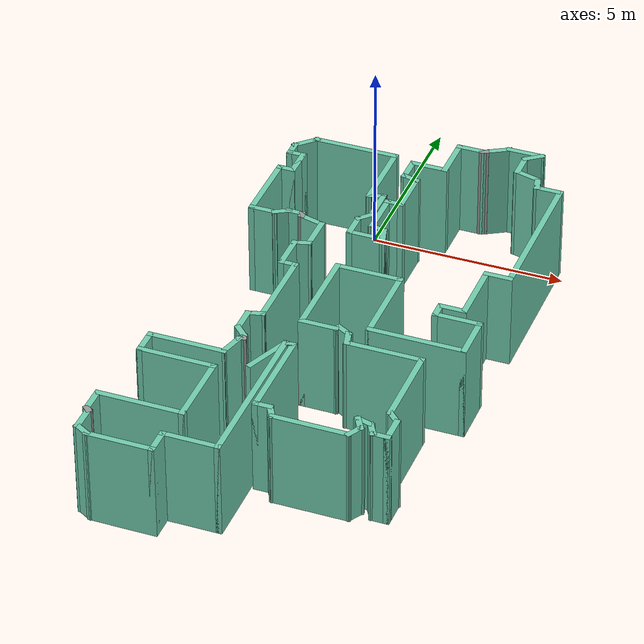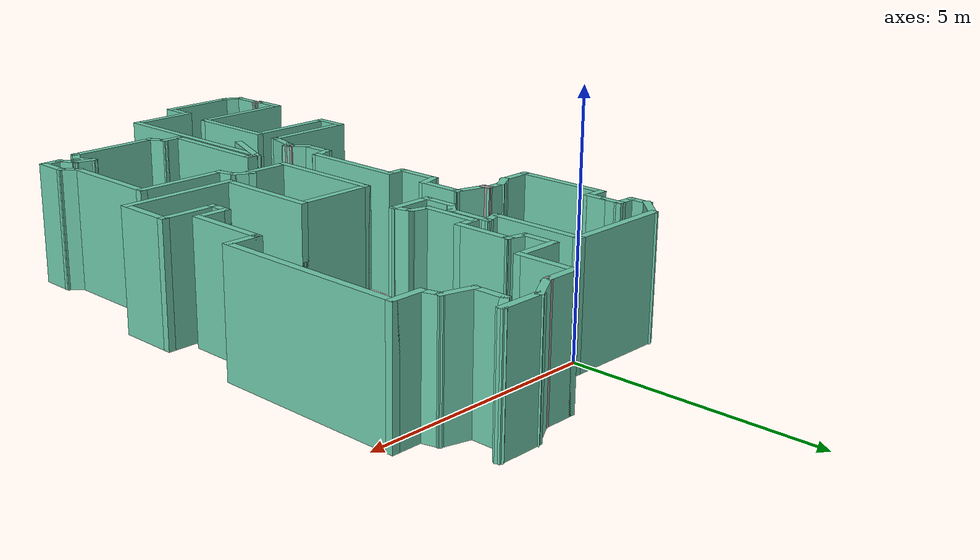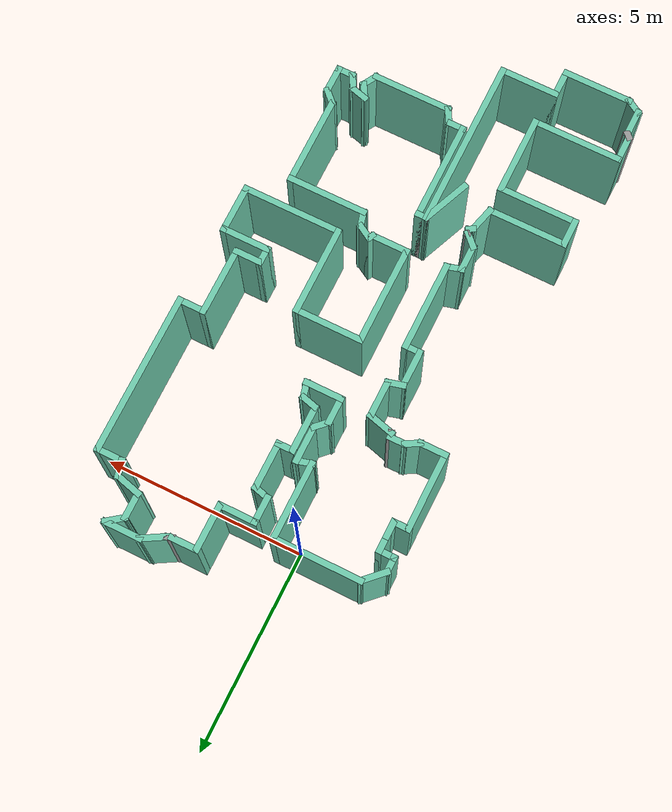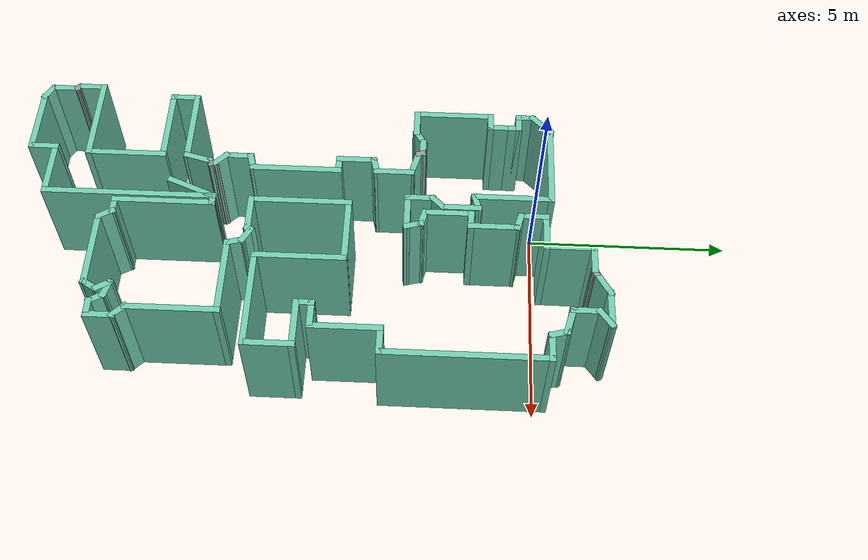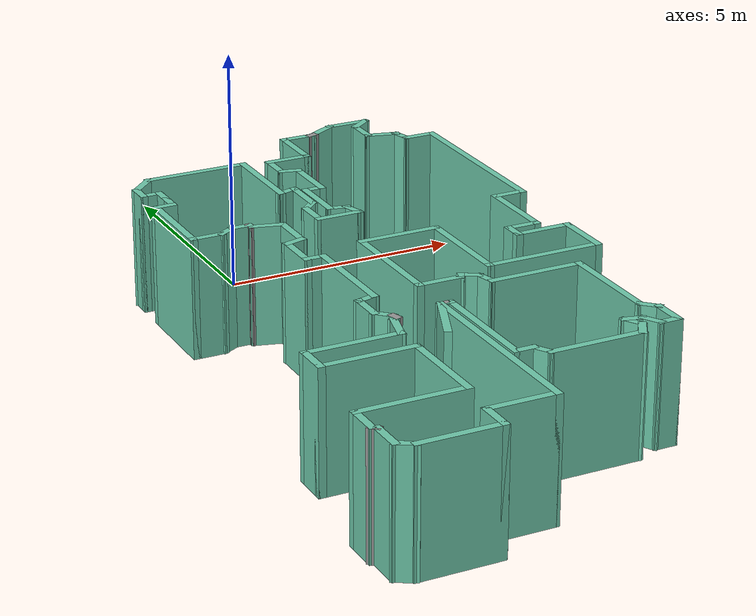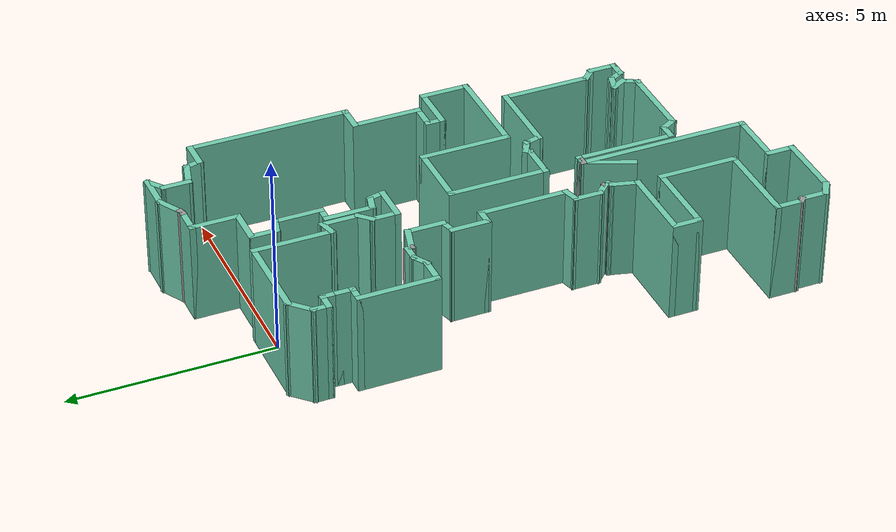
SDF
<?xml version='1.0'?>
<sdf version='1.6'>
  <model name='map_7'>
    <pose frame=''>1.04901 -5.45301 0 0 -0 0</pose>
    <link name='Wall_0'>
      <collision name='Wall_0_Collision'>
        <geometry>
          <box>
            <size>1 0.15 2.5</size>
          </box>
        </geometry>
        <pose frame=''>0 0 1.25 0 -0 0</pose>
      </collision>
      <visual name='Wall_0_Visual'>
        <pose frame=''>0 0 1.25 0 -0 0</pose>
        <geometry>
          <box>
            <size>1 0.15 2.5</size>
          </box>
        </geometry>
        <material>
          <script>
            <uri>file://media/materials/scripts/gazebo.material</uri>
            <name>Gazebo/Grey</name>
          </script>
          <ambient>0.435294 0.796078 0.67451 1</ambient>
        </material>
        <meta>
          <layer>0</layer>
        </meta>
      </visual>
      <pose frame=''>2.38063 7.06866 0 0 -0 3.14159</pose>
    </link>
    <link name='Wall_1'>
      <collision name='Wall_1_Collision'>
        <geometry>
          <box>
            <size>0.75 0.15 2.5</size>
          </box>
        </geometry>
        <pose frame=''>0 0 1.25 0 -0 0</pose>
      </collision>
      <visual name='Wall_1_Visual'>
        <pose frame=''>0 0 1.25 0 -0 0</pose>
        <geometry>
          <box>
            <size>0.75 0.15 2.5</size>
          </box>
        </geometry>
        <material>
          <script>
            <uri>file://media/materials/scripts/gazebo.material</uri>
            <name>Gazebo/Grey</name>
          </script>
          <ambient>0.435294 0.796078 0.67451 1</ambient>
        </material>
        <meta>
          <layer>0</layer>
        </meta>
      </visual>
      <pose frame=''>1.69582 6.91866 0 0 -0 -2.61799</pose>
    </link>
    <link name='Wall_10'>
      <collision name='Wall_10_Collision'>
        <geometry>
          <box>
            <size>1.25 0.15 2.5</size>
          </box>
        </geometry>
        <pose frame=''>0 0 1.25 0 -0 0</pose>
      </collision>
      <visual name='Wall_10_Visual'>
        <pose frame=''>0 0 1.25 0 -0 0</pose>
        <geometry>
          <box>
            <size>1.25 0.15 2.5</size>
          </box>
        </geometry>
        <material>
          <script>
            <uri>file://media/materials/scripts/gazebo.material</uri>
            <name>Gazebo/Grey</name>
          </script>
          <ambient>0.435294 0.796078 0.67451 1</ambient>
        </material>
        <meta>
          <layer>0</layer>
        </meta>
      </visual>
      <pose frame=''>0.73942 6.19278 0 0 -0 -1.5708</pose>
    </link>
    <link name='Wall_100'>
      <collision name='Wall_100_Collision'>
        <geometry>
          <box>
            <size>0.5 0.15 2.5</size>
          </box>
        </geometry>
        <pose frame=''>0 0 1.25 0 -0 0</pose>
      </collision>
      <visual name='Wall_100_Visual'>
        <pose frame=''>0 0 1.25 0 -0 0</pose>
        <geometry>
          <box>
            <size>0.5 0.15 2.5</size>
          </box>
        </geometry>
        <material>
          <script>
            <uri>file://media/materials/scripts/gazebo.material</uri>
            <name>Gazebo/Grey</name>
          </script>
          <ambient>0.435294 0.796078 0.67451 1</ambient>
        </material>
        <meta>
          <layer>0</layer>
        </meta>
      </visual>
      <pose frame=''>0.92429 -1.69529 0 0 -0 1.8326</pose>
    </link>
    <link name='Wall_101'>
      <collision name='Wall_101_Collision'>
        <geometry>
          <box>
            <size>0.5 0.15 2.5</size>
          </box>
        </geometry>
        <pose frame=''>0 0 1.25 0 -0 0</pose>
      </collision>
      <visual name='Wall_101_Visual'>
        <pose frame=''>0 0 1.25 0 -0 0</pose>
        <geometry>
          <box>
            <size>0.5 0.15 2.5</size>
          </box>
        </geometry>
        <material>
          <script>
            <uri>file://media/materials/scripts/gazebo.material</uri>
            <name>Gazebo/Grey</name>
          </script>
          <ambient>0.435294 0.796078 0.67451 1</ambient>
        </material>
        <meta>
          <layer>0</layer>
        </meta>
      </visual>
      <pose frame=''>0.727443 -1.43876 0 0 -0 2.61799</pose>
    </link>
    <link name='Wall_102'>
      <collision name='Wall_102_Collision'>
        <geometry>
          <box>
            <size>0.25 0.15 2.5</size>
          </box>
        </geometry>
        <pose frame=''>0 0 1.25 0 -0 0</pose>
      </collision>
      <visual name='Wall_102_Visual'>
        <pose frame=''>0 0 1.25 0 -0 0</pose>
        <geometry>
          <box>
            <size>0.25 0.15 2.5</size>
          </box>
        </geometry>
        <material>
          <script>
            <uri>file://media/materials/scripts/gazebo.material</uri>
            <name>Gazebo/Grey</name>
          </script>
          <ambient>0.435294 0.796078 0.67451 1</ambient>
        </material>
        <meta>
          <layer>0</layer>
        </meta>
      </visual>
      <pose frame=''>0.550888 -1.39456 0 0 -0 -2.0944</pose>
    </link>
    <link name='Wall_103'>
      <collision name='Wall_103_Collision'>
        <geometry>
          <box>
            <size>1 0.15 2.5</size>
          </box>
        </geometry>
        <pose frame=''>0 0 1.25 0 -0 0</pose>
      </collision>
      <visual name='Wall_103_Visual'>
        <pose frame=''>0 0 1.25 0 -0 0</pose>
        <geometry>
          <box>
            <size>1 0.15 2.5</size>
          </box>
        </geometry>
        <material>
          <script>
            <uri>file://media/materials/scripts/gazebo.material</uri>
            <name>Gazebo/Grey</name>
          </script>
          <ambient>0.435294 0.796078 0.67451 1</ambient>
        </material>
        <meta>
          <layer>0</layer>
        </meta>
      </visual>
      <pose frame=''>0.100888 -1.43786 0 0 -0 3.14159</pose>
    </link>
    <link name='Wall_104'>
      <collision name='Wall_104_Collision'>
        <geometry>
          <box>
            <size>2.5 0.15 2.5</size>
          </box>
        </geometry>
        <pose frame=''>0 0 1.25 0 -0 0</pose>
      </collision>
      <visual name='Wall_104_Visual'>
        <pose frame=''>0 0 1.25 0 -0 0</pose>
        <geometry>
          <box>
            <size>2.5 0.15 2.5</size>
          </box>
        </geometry>
        <material>
          <script>
            <uri>file://media/materials/scripts/gazebo.material</uri>
            <name>Gazebo/Grey</name>
          </script>
          <ambient>0.435294 0.796078 0.67451 1</ambient>
        </material>
        <meta>
          <layer>0</layer>
        </meta>
      </visual>
      <pose frame=''>-0.324112 -0.26286 0 0 -0 1.5708</pose>
    </link>
    <link name='Wall_105'>
      <collision name='Wall_105_Collision'>
        <geometry>
          <box>
            <size>1.75 0.15 2.5</size>
          </box>
        </geometry>
        <pose frame=''>0 0 1.25 0 -0 0</pose>
      </collision>
      <visual name='Wall_105_Visual'>
        <pose frame=''>0 0 1.25 0 -0 0</pose>
        <geometry>
          <box>
            <size>1.75 0.15 2.5</size>
          </box>
        </geometry>
        <material>
          <script>
            <uri>file://media/materials/scripts/gazebo.material</uri>
            <name>Gazebo/Grey</name>
          </script>
          <ambient>0.435294 0.796078 0.67451 1</ambient>
        </material>
        <meta>
          <layer>0</layer>
        </meta>
      </visual>
      <pose frame=''>0.475888 0.91214 0 0 -0 0</pose>
    </link>
    <link name='Wall_106'>
      <collision name='Wall_106_Collision'>
        <geometry>
          <box>
            <size>2.25 0.15 2.5</size>
          </box>
        </geometry>
        <pose frame=''>0 0 1.25 0 -0 0</pose>
      </collision>
      <visual name='Wall_106_Visual'>
        <pose frame=''>0 0 1.25 0 -0 0</pose>
        <geometry>
          <box>
            <size>2.25 0.15 2.5</size>
          </box>
        </geometry>
        <material>
          <script>
            <uri>file://media/materials/scripts/gazebo.material</uri>
            <name>Gazebo/Grey</name>
          </script>
          <ambient>0.435294 0.796078 0.67451 1</ambient>
        </material>
        <meta>
          <layer>0</layer>
        </meta>
      </visual>
      <pose frame=''>1.27589 -0.13786 0 0 -0 -1.5708</pose>
    </link>
    <link name='Wall_107'>
      <collision name='Wall_107_Collision'>
        <geometry>
          <box>
            <size>2.5 0.15 2.5</size>
          </box>
        </geometry>
        <pose frame=''>0 0 1.25 0 -0 0</pose>
      </collision>
      <visual name='Wall_107_Visual'>
        <pose frame=''>0 0 1.25 0 -0 0</pose>
        <geometry>
          <box>
            <size>2.5 0.15 2.5</size>
          </box>
        </geometry>
        <material>
          <script>
            <uri>file://media/materials/scripts/gazebo.material</uri>
            <name>Gazebo/Grey</name>
          </script>
          <ambient>0.435294 0.796078 0.67451 1</ambient>
        </material>
        <meta>
          <layer>0</layer>
        </meta>
      </visual>
      <pose frame=''>2.45089 -1.18786 0 0 -0 0</pose>
    </link>
    <link name='Wall_108'>
      <collision name='Wall_108_Collision'>
        <geometry>
          <box>
            <size>1.25 0.15 2.5</size>
          </box>
        </geometry>
        <pose frame=''>0 0 1.25 0 -0 0</pose>
      </collision>
      <visual name='Wall_108_Visual'>
        <pose frame=''>0 0 1.25 0 -0 0</pose>
        <geometry>
          <box>
            <size>1.25 0.15 2.5</size>
          </box>
        </geometry>
        <material>
          <script>
            <uri>file://media/materials/scripts/gazebo.material</uri>
            <name>Gazebo/Grey</name>
          </script>
          <ambient>0.435294 0.796078 0.67451 1</ambient>
        </material>
        <meta>
          <layer>0</layer>
        </meta>
      </visual>
      <pose frame=''>3.62589 -0.63786 0 0 -0 1.5708</pose>
    </link>
    <link name='Wall_109'>
      <collision name='Wall_109_Collision'>
        <geometry>
          <box>
            <size>1.25 0.15 2.5</size>
          </box>
        </geometry>
        <pose frame=''>0 0 1.25 0 -0 0</pose>
      </collision>
      <visual name='Wall_109_Visual'>
        <pose frame=''>0 0 1.25 0 -0 0</pose>
        <geometry>
          <box>
            <size>1.25 0.15 2.5</size>
          </box>
        </geometry>
        <material>
          <script>
            <uri>file://media/materials/scripts/gazebo.material</uri>
            <name>Gazebo/Grey</name>
          </script>
          <ambient>0.435294 0.796078 0.67451 1</ambient>
        </material>
        <meta>
          <layer>0</layer>
        </meta>
      </visual>
      <pose frame=''>3.07589 -0.08786 0 0 -0 3.14159</pose>
    </link>
    <link name='Wall_11'>
      <collision name='Wall_11_Collision'>
        <geometry>
          <box>
            <size>1 0.15 2.5</size>
          </box>
        </geometry>
        <pose frame=''>0 0 1.25 0 -0 0</pose>
      </collision>
      <visual name='Wall_11_Visual'>
        <pose frame=''>0 0 1.25 0 -0 0</pose>
        <geometry>
          <box>
            <size>1 0.15 2.5</size>
          </box>
        </geometry>
        <material>
          <script>
            <uri>file://media/materials/scripts/gazebo.material</uri>
            <name>Gazebo/Grey</name>
          </script>
          <ambient>0.435294 0.796078 0.67451 1</ambient>
        </material>
        <meta>
          <layer>0</layer>
        </meta>
      </visual>
      <pose frame=''>0.31442 5.64278 0 0 -0 3.14159</pose>
    </link>
    <link name='Wall_110'>
      <collision name='Wall_110_Collision'>
        <geometry>
          <box>
            <size>0.5 0.15 2.5</size>
          </box>
        </geometry>
        <pose frame=''>0 0 1.25 0 -0 0</pose>
      </collision>
      <visual name='Wall_110_Visual'>
        <pose frame=''>0 0 1.25 0 -0 0</pose>
        <geometry>
          <box>
            <size>0.5 0.15 2.5</size>
          </box>
        </geometry>
        <material>
          <script>
            <uri>file://media/materials/scripts/gazebo.material</uri>
            <name>Gazebo/Grey</name>
          </script>
          <ambient>0.435294 0.796078 0.67451 1</ambient>
        </material>
        <meta>
          <layer>0</layer>
        </meta>
      </visual>
      <pose frame=''>2.52589 0.08714 0 0 -0 1.5708</pose>
    </link>
    <link name='Wall_111'>
      <collision name='Wall_111_Collision'>
        <geometry>
          <box>
            <size>0.75 0.15 2.5</size>
          </box>
        </geometry>
        <pose frame=''>0 0 1.25 0 -0 0</pose>
      </collision>
      <visual name='Wall_111_Visual'>
        <pose frame=''>0 0 1.25 0 -0 0</pose>
        <geometry>
          <box>
            <size>0.75 0.15 2.5</size>
          </box>
        </geometry>
        <material>
          <script>
            <uri>file://media/materials/scripts/gazebo.material</uri>
            <name>Gazebo/Grey</name>
          </script>
          <ambient>0.435294 0.796078 0.67451 1</ambient>
        </material>
        <meta>
          <layer>0</layer>
        </meta>
      </visual>
      <pose frame=''>2.82589 0.26214 0 0 -0 0</pose>
    </link>
    <link name='Wall_112'>
      <collision name='Wall_112_Collision'>
        <geometry>
          <box>
            <size>1.75 0.15 2.5</size>
          </box>
        </geometry>
        <pose frame=''>0 0 1.25 0 -0 0</pose>
      </collision>
      <visual name='Wall_112_Visual'>
        <pose frame=''>0 0 1.25 0 -0 0</pose>
        <geometry>
          <box>
            <size>1.75 0.15 2.5</size>
          </box>
        </geometry>
        <material>
          <script>
            <uri>file://media/materials/scripts/gazebo.material</uri>
            <name>Gazebo/Grey</name>
          </script>
          <ambient>0.435294 0.796078 0.67451 1</ambient>
        </material>
        <meta>
          <layer>0</layer>
        </meta>
      </visual>
      <pose frame=''>3.12589 1.06214 0 0 -0 1.5708</pose>
    </link>
    <link name='Wall_115'>
      <collision name='Wall_115_Collision'>
        <geometry>
          <box>
            <size>0.75 0.15 2.5</size>
          </box>
        </geometry>
        <pose frame=''>0 0 1.25 0 -0 0</pose>
      </collision>
      <visual name='Wall_115_Visual'>
        <pose frame=''>0 0 1.25 0 -0 0</pose>
        <geometry>
          <box>
            <size>0.75 0.15 2.5</size>
          </box>
        </geometry>
        <material>
          <script>
            <uri>file://media/materials/scripts/gazebo.material</uri>
            <name>Gazebo/Grey</name>
          </script>
          <ambient>0.435294 0.796078 0.67451 1</ambient>
        </material>
        <meta>
          <layer>0</layer>
        </meta>
      </visual>
      <pose frame=''>3.42589 1.86214 0 0 -0 0</pose>
    </link>
    <link name='Wall_116'>
      <collision name='Wall_116_Collision'>
        <geometry>
          <box>
            <size>4 0.15 2.5</size>
          </box>
        </geometry>
        <pose frame=''>0 0 1.25 0 -0 0</pose>
      </collision>
      <visual name='Wall_116_Visual'>
        <pose frame=''>0 0 1.25 0 -0 0</pose>
        <geometry>
          <box>
            <size>4 0.15 2.5</size>
          </box>
        </geometry>
        <material>
          <script>
            <uri>file://media/materials/scripts/gazebo.material</uri>
            <name>Gazebo/Grey</name>
          </script>
          <ambient>0.435294 0.796078 0.67451 1</ambient>
        </material>
        <meta>
          <layer>0</layer>
        </meta>
      </visual>
      <pose frame=''>3.72589 3.78714 0 0 -0 1.5708</pose>
    </link>
    <link name='Wall_117'>
      <collision name='Wall_117_Collision'>
        <geometry>
          <box>
            <size>0.75 0.15 2.5</size>
          </box>
        </geometry>
        <pose frame=''>0 0 1.25 0 -0 0</pose>
      </collision>
      <visual name='Wall_117_Visual'>
        <pose frame=''>0 0 1.25 0 -0 0</pose>
        <geometry>
          <box>
            <size>0.75 0.15 2.5</size>
          </box>
        </geometry>
        <material>
          <script>
            <uri>file://media/materials/scripts/gazebo.material</uri>
            <name>Gazebo/Grey</name>
          </script>
          <ambient>0.435294 0.796078 0.67451 1</ambient>
        </material>
        <meta>
          <layer>0</layer>
        </meta>
      </visual>
      <pose frame=''>3.42589 5.71214 0 0 -0 3.14159</pose>
    </link>
    <link name='Wall_118'>
      <collision name='Wall_118_Collision'>
        <geometry>
          <box>
            <size>0.5 0.15 2.5</size>
          </box>
        </geometry>
        <pose frame=''>0 0 1.25 0 -0 0</pose>
      </collision>
      <visual name='Wall_118_Visual'>
        <pose frame=''>0 0 1.25 0 -0 0</pose>
        <geometry>
          <box>
            <size>0.5 0.15 2.5</size>
          </box>
        </geometry>
        <material>
          <script>
            <uri>file://media/materials/scripts/gazebo.material</uri>
            <name>Gazebo/Grey</name>
          </script>
          <ambient>0.435294 0.796078 0.67451 1</ambient>
        </material>
        <meta>
          <layer>0</layer>
        </meta>
      </visual>
      <pose frame=''>3.0806 5.88118 0 0 -0 1.8326</pose>
    </link>
    <link name='Wall_119'>
      <collision name='Wall_119_Collision'>
        <geometry>
          <box>
            <size>0.75 0.15 2.5</size>
          </box>
        </geometry>
        <pose frame=''>0 0 1.25 0 -0 0</pose>
      </collision>
      <visual name='Wall_119_Visual'>
        <pose frame=''>0 0 1.25 0 -0 0</pose>
        <geometry>
          <box>
            <size>0.75 0.15 2.5</size>
          </box>
        </geometry>
        <material>
          <script>
            <uri>file://media/materials/scripts/gazebo.material</uri>
            <name>Gazebo/Grey</name>
          </script>
          <ambient>0.435294 0.796078 0.67451 1</ambient>
        </material>
        <meta>
          <layer>0</layer>
        </meta>
      </visual>
      <pose frame=''>2.74552 6.12786 0 0 -0 2.87979</pose>
    </link>
    <link name='Wall_122'>
      <collision name='Wall_122_Collision'>
        <geometry>
          <box>
            <size>0.75 0.15 2.5</size>
          </box>
        </geometry>
        <pose frame=''>0 0 1.25 0 -0 0</pose>
      </collision>
      <visual name='Wall_122_Visual'>
        <pose frame=''>0 0 1.25 0 -0 0</pose>
        <geometry>
          <box>
            <size>0.75 0.15 2.5</size>
          </box>
        </geometry>
        <material>
          <script>
            <uri>file://media/materials/scripts/gazebo.material</uri>
            <name>Gazebo/Grey</name>
          </script>
          <ambient>0.435294 0.796078 0.67451 1</ambient>
        </material>
        <meta>
          <layer>0</layer>
        </meta>
      </visual>
      <pose frame=''>2.45575 6.50551 0 0 -0 1.5708</pose>
    </link>
    <link name='Wall_123'>
      <collision name='Wall_123_Collision'>
        <geometry>
          <box>
            <size>0.587801 0.15 2.5</size>
          </box>
        </geometry>
        <pose frame=''>0 0 1.25 0 -0 0</pose>
      </collision>
      <visual name='Wall_123_Visual'>
        <pose frame=''>0 0 1.25 0 -0 0</pose>
        <geometry>
          <box>
            <size>0.587801 0.15 2.5</size>
          </box>
        </geometry>
        <material>
          <script>
            <uri>file://media/materials/scripts/gazebo.material</uri>
            <name>Gazebo/Grey</name>
          </script>
          <ambient>0.435294 0.796078 0.67451 1</ambient>
        </material>
        <meta>
          <layer>0</layer>
        </meta>
      </visual>
      <pose frame=''>2.63069 6.93708 0 0 -0 0.644866</pose>
    </link>
    <link name='Wall_125'>
      <collision name='Wall_125_Collision'>
        <geometry>
          <box>
            <size>1.32079 0.15 2.5</size>
          </box>
        </geometry>
        <pose frame=''>0 0 1.25 0 -0 0</pose>
      </collision>
      <visual name='Wall_125_Visual'>
        <pose frame=''>0 0 1.25 0 -0 0</pose>
        <geometry>
          <box>
            <size>1.32079 0.15 2.5</size>
          </box>
        </geometry>
        <material>
          <script>
            <uri>file://media/materials/scripts/gazebo.material</uri>
            <name>Gazebo/Grey</name>
          </script>
          <ambient>0.435294 0.796078 0.67451 1</ambient>
        </material>
        <meta>
          <layer>0</layer>
        </meta>
      </visual>
      <pose frame=''>-0.594171 -2.91242 0 0 -0 1.17967</pose>
    </link>
    <link name='Wall_16'>
      <collision name='Wall_16_Collision'>
        <geometry>
          <box>
            <size>0.75 0.15 2.5</size>
          </box>
        </geometry>
        <pose frame=''>0 0 1.25 0 -0 0</pose>
      </collision>
      <visual name='Wall_16_Visual'>
        <pose frame=''>0 0 1.25 0 -0 0</pose>
        <geometry>
          <box>
            <size>0.75 0.15 2.5</size>
          </box>
        </geometry>
        <material>
          <script>
            <uri>file://media/materials/scripts/gazebo.material</uri>
            <name>Gazebo/Grey</name>
          </script>
          <ambient>0.435294 0.796078 0.67451 1</ambient>
        </material>
        <meta>
          <layer>0</layer>
        </meta>
      </visual>
      <pose frame=''>-0.11058 5.34278 0 0 -0 -1.5708</pose>
    </link>
    <link name='Wall_17'>
      <collision name='Wall_17_Collision'>
        <geometry>
          <box>
            <size>0.5 0.15 2.5</size>
          </box>
        </geometry>
        <pose frame=''>0 0 1.25 0 -0 0</pose>
      </collision>
      <visual name='Wall_17_Visual'>
        <pose frame=''>0 0 1.25 0 -0 0</pose>
        <geometry>
          <box>
            <size>0.5 0.15 2.5</size>
          </box>
        </geometry>
        <material>
          <script>
            <uri>file://media/materials/scripts/gazebo.material</uri>
            <name>Gazebo/Grey</name>
          </script>
          <ambient>0.435294 0.796078 0.67451 1</ambient>
        </material>
        <meta>
          <layer>0</layer>
        </meta>
      </visual>
      <pose frame=''>0.058457 4.99749 0 0 -0 -0.261799</pose>
    </link>
    <link name='Wall_18'>
      <collision name='Wall_18_Collision'>
        <geometry>
          <box>
            <size>1.25 0.15 2.5</size>
          </box>
        </geometry>
        <pose frame=''>0 0 1.25 0 -0 0</pose>
      </collision>
      <visual name='Wall_18_Visual'>
        <pose frame=''>0 0 1.25 0 -0 0</pose>
        <geometry>
          <box>
            <size>1.25 0.15 2.5</size>
          </box>
        </geometry>
        <material>
          <script>
            <uri>file://media/materials/scripts/gazebo.material</uri>
            <name>Gazebo/Grey</name>
          </script>
          <ambient>0.435294 0.796078 0.67451 1</ambient>
        </material>
        <meta>
          <layer>0</layer>
        </meta>
      </visual>
      <pose frame=''>0.227494 4.40219 0 0 -0 -1.5708</pose>
    </link>
    <link name='Wall_19'>
      <collision name='Wall_19_Collision'>
        <geometry>
          <box>
            <size>0.5 0.15 2.5</size>
          </box>
        </geometry>
        <pose frame=''>0 0 1.25 0 -0 0</pose>
      </collision>
      <visual name='Wall_19_Visual'>
        <pose frame=''>0 0 1.25 0 -0 0</pose>
        <geometry>
          <box>
            <size>0.5 0.15 2.5</size>
          </box>
        </geometry>
        <material>
          <script>
            <uri>file://media/materials/scripts/gazebo.material</uri>
            <name>Gazebo/Grey</name>
          </script>
          <ambient>0.435294 0.796078 0.67451 1</ambient>
        </material>
        <meta>
          <layer>0</layer>
        </meta>
      </visual>
      <pose frame=''>0.052494 3.8522 0 0 -0 3.14159</pose>
    </link>
    <link name='Wall_20'>
      <collision name='Wall_20_Collision'>
        <geometry>
          <box>
            <size>1.25 0.15 2.5</size>
          </box>
        </geometry>
        <pose frame=''>0 0 1.25 0 -0 0</pose>
      </collision>
      <visual name='Wall_20_Visual'>
        <pose frame=''>0 0 1.25 0 -0 0</pose>
        <geometry>
          <box>
            <size>1.25 0.15 2.5</size>
          </box>
        </geometry>
        <material>
          <script>
            <uri>file://media/materials/scripts/gazebo.material</uri>
            <name>Gazebo/Grey</name>
          </script>
          <ambient>0.435294 0.796078 0.67451 1</ambient>
        </material>
        <meta>
          <layer>0</layer>
        </meta>
      </visual>
      <pose frame=''>-0.122506 3.3022 0 0 -0 -1.5708</pose>
    </link>
    <link name='Wall_21'>
      <collision name='Wall_21_Collision'>
        <geometry>
          <box>
            <size>0.5 0.15 2.5</size>
          </box>
        </geometry>
        <pose frame=''>0 0 1.25 0 -0 0</pose>
      </collision>
      <visual name='Wall_21_Visual'>
        <pose frame=''>0 0 1.25 0 -0 0</pose>
        <geometry>
          <box>
            <size>0.5 0.15 2.5</size>
          </box>
        </geometry>
        <material>
          <script>
            <uri>file://media/materials/scripts/gazebo.material</uri>
            <name>Gazebo/Grey</name>
          </script>
          <ambient>0.435294 0.796078 0.67451 1</ambient>
        </material>
        <meta>
          <layer>0</layer>
        </meta>
      </visual>
      <pose frame=''>0.046531 2.7069 0 0 -0 -0.261799</pose>
    </link>
    <link name='Wall_22'>
      <collision name='Wall_22_Collision'>
        <geometry>
          <box>
            <size>0.5 0.15 2.5</size>
          </box>
        </geometry>
        <pose frame=''>0 0 1.25 0 -0 0</pose>
      </collision>
      <visual name='Wall_22_Visual'>
        <pose frame=''>0 0 1.25 0 -0 0</pose>
        <geometry>
          <box>
            <size>0.5 0.15 2.5</size>
          </box>
        </geometry>
        <material>
          <script>
            <uri>file://media/materials/scripts/gazebo.material</uri>
            <name>Gazebo/Grey</name>
          </script>
          <ambient>0.435294 0.796078 0.67451 1</ambient>
        </material>
        <meta>
          <layer>0</layer>
        </meta>
      </visual>
      <pose frame=''>0.260861 2.49257 0 0 -0 -1.309</pose>
    </link>
    <link name='Wall_25'>
      <collision name='Wall_25_Collision'>
        <geometry>
          <box>
            <size>1 0.15 2.5</size>
          </box>
        </geometry>
        <pose frame=''>0 0 1.25 0 -0 0</pose>
      </collision>
      <visual name='Wall_25_Visual'>
        <pose frame=''>0 0 1.25 0 -0 0</pose>
        <geometry>
          <box>
            <size>1 0.15 2.5</size>
          </box>
        </geometry>
        <material>
          <script>
            <uri>file://media/materials/scripts/gazebo.material</uri>
            <name>Gazebo/Grey</name>
          </script>
          <ambient>0.435294 0.796078 0.67451 1</ambient>
        </material>
        <meta>
          <layer>0</layer>
        </meta>
      </visual>
      <pose frame=''>-0.118845 2.32353 0 0 -0 3.14159</pose>
    </link>
    <link name='Wall_26'>
      <collision name='Wall_26_Collision'>
        <geometry>
          <box>
            <size>0.75 0.15 2.5</size>
          </box>
        </geometry>
        <pose frame=''>0 0 1.25 0 -0 0</pose>
      </collision>
      <visual name='Wall_26_Visual'>
        <pose frame=''>0 0 1.25 0 -0 0</pose>
        <geometry>
          <box>
            <size>0.75 0.15 2.5</size>
          </box>
        </geometry>
        <material>
          <script>
            <uri>file://media/materials/scripts/gazebo.material</uri>
            <name>Gazebo/Grey</name>
          </script>
          <ambient>0.435294 0.796078 0.67451 1</ambient>
        </material>
        <meta>
          <layer>0</layer>
        </meta>
      </visual>
      <pose frame=''>-0.543845 2.62353 0 0 -0 1.5708</pose>
    </link>
    <link name='Wall_29'>
      <collision name='Wall_29_Collision'>
        <geometry>
          <box>
            <size>0.5 0.15 2.5</size>
          </box>
        </geometry>
        <pose frame=''>0 0 1.25 0 -0 0</pose>
      </collision>
      <visual name='Wall_29_Visual'>
        <pose frame=''>0 0 1.25 0 -0 0</pose>
        <geometry>
          <box>
            <size>0.5 0.15 2.5</size>
          </box>
        </geometry>
        <material>
          <script>
            <uri>file://media/materials/scripts/gazebo.material</uri>
            <name>Gazebo/Grey</name>
          </script>
          <ambient>0.435294 0.796078 0.67451 1</ambient>
        </material>
        <meta>
          <layer>0</layer>
        </meta>
      </visual>
      <pose frame=''>-0.420102 3.04728 0 0 -0 0.785398</pose>
    </link>
    <link name='Wall_30'>
      <collision name='Wall_30_Collision'>
        <geometry>
          <box>
            <size>1 0.15 2.5</size>
          </box>
        </geometry>
        <pose frame=''>0 0 1.25 0 -0 0</pose>
      </collision>
      <visual name='Wall_30_Visual'>
        <pose frame=''>0 0 1.25 0 -0 0</pose>
        <geometry>
          <box>
            <size>1 0.15 2.5</size>
          </box>
        </geometry>
        <material>
          <script>
            <uri>file://media/materials/scripts/gazebo.material</uri>
            <name>Gazebo/Grey</name>
          </script>
          <ambient>0.435294 0.796078 0.67451 1</ambient>
        </material>
        <meta>
          <layer>0</layer>
        </meta>
      </visual>
      <pose frame=''>-0.296358 3.59602 0 0 -0 1.5708</pose>
    </link>
    <link name='Wall_31'>
      <collision name='Wall_31_Collision'>
        <geometry>
          <box>
            <size>0.5 0.15 2.5</size>
          </box>
        </geometry>
        <pose frame=''>0 0 1.25 0 -0 0</pose>
      </collision>
      <visual name='Wall_31_Visual'>
        <pose frame=''>0 0 1.25 0 -0 0</pose>
        <geometry>
          <box>
            <size>0.5 0.15 2.5</size>
          </box>
        </geometry>
        <material>
          <script>
            <uri>file://media/materials/scripts/gazebo.material</uri>
            <name>Gazebo/Grey</name>
          </script>
          <ambient>0.435294 0.796078 0.67451 1</ambient>
        </material>
        <meta>
          <layer>0</layer>
        </meta>
      </visual>
      <pose frame=''>-0.465395 3.97573 0 0 -0 -2.87979</pose>
    </link>
    <link name='Wall_32'>
      <collision name='Wall_32_Collision'>
        <geometry>
          <box>
            <size>2 0.15 2.5</size>
          </box>
        </geometry>
        <pose frame=''>0 0 1.25 0 -0 0</pose>
      </collision>
      <visual name='Wall_32_Visual'>
        <pose frame=''>0 0 1.25 0 -0 0</pose>
        <geometry>
          <box>
            <size>2 0.15 2.5</size>
          </box>
        </geometry>
        <material>
          <script>
            <uri>file://media/materials/scripts/gazebo.material</uri>
            <name>Gazebo/Grey</name>
          </script>
          <ambient>0.435294 0.796078 0.67451 1</ambient>
        </material>
        <meta>
          <layer>0</layer>
        </meta>
      </visual>
      <pose frame=''>-0.634432 4.85543 0 0 -0 1.5708</pose>
    </link>
    <link name='Wall_33'>
      <collision name='Wall_33_Collision'>
        <geometry>
          <box>
            <size>2.25 0.15 2.5</size>
          </box>
        </geometry>
        <pose frame=''>0 0 1.25 0 -0 0</pose>
      </collision>
      <visual name='Wall_33_Visual'>
        <pose frame=''>0 0 1.25 0 -0 0</pose>
        <geometry>
          <box>
            <size>2.25 0.15 2.5</size>
          </box>
        </geometry>
        <material>
          <script>
            <uri>file://media/materials/scripts/gazebo.material</uri>
            <name>Gazebo/Grey</name>
          </script>
          <ambient>0.435294 0.796078 0.67451 1</ambient>
        </material>
        <meta>
          <layer>0</layer>
        </meta>
      </visual>
      <pose frame=''>-1.68443 5.78043 0 0 -0 3.14159</pose>
    </link>
    <link name='Wall_34'>
      <collision name='Wall_34_Collision'>
        <geometry>
          <box>
            <size>0.75 0.15 2.5</size>
          </box>
        </geometry>
        <pose frame=''>0 0 1.25 0 -0 0</pose>
      </collision>
      <visual name='Wall_34_Visual'>
        <pose frame=''>0 0 1.25 0 -0 0</pose>
        <geometry>
          <box>
            <size>0.75 0.15 2.5</size>
          </box>
        </geometry>
        <material>
          <script>
            <uri>file://media/materials/scripts/gazebo.material</uri>
            <name>Gazebo/Grey</name>
          </script>
          <ambient>0.435294 0.796078 0.67451 1</ambient>
        </material>
        <meta>
          <layer>0</layer>
        </meta>
      </visual>
      <pose frame=''>-2.94656 5.5683 0 0 -0 -2.35619</pose>
    </link>
    <link name='Wall_35'>
      <collision name='Wall_35_Collision'>
        <geometry>
          <box>
            <size>0.5 0.15 2.5</size>
          </box>
        </geometry>
        <pose frame=''>0 0 1.25 0 -0 0</pose>
      </collision>
      <visual name='Wall_35_Visual'>
        <pose frame=''>0 0 1.25 0 -0 0</pose>
        <geometry>
          <box>
            <size>0.5 0.15 2.5</size>
          </box>
        </geometry>
        <material>
          <script>
            <uri>file://media/materials/scripts/gazebo.material</uri>
            <name>Gazebo/Grey</name>
          </script>
          <ambient>0.435294 0.796078 0.67451 1</ambient>
        </material>
        <meta>
          <layer>0</layer>
        </meta>
      </visual>
      <pose frame=''>-3.1587 5.18117 0 0 -0 -1.5708</pose>
    </link>
    <link name='Wall_36'>
      <collision name='Wall_36_Collision'>
        <geometry>
          <box>
            <size>0.5 0.15 2.5</size>
          </box>
        </geometry>
        <pose frame=''>0 0 1.25 0 -0 0</pose>
      </collision>
      <visual name='Wall_36_Visual'>
        <pose frame=''>0 0 1.25 0 -0 0</pose>
        <geometry>
          <box>
            <size>0.5 0.15 2.5</size>
          </box>
        </geometry>
        <material>
          <script>
            <uri>file://media/materials/scripts/gazebo.material</uri>
            <name>Gazebo/Grey</name>
          </script>
          <ambient>0.435294 0.796078 0.67451 1</ambient>
        </material>
        <meta>
          <layer>0</layer>
        </meta>
      </visual>
      <pose frame=''>-2.9837 5.00617 0 0 -0 0</pose>
    </link>
    <link name='Wall_37'>
      <collision name='Wall_37_Collision'>
        <geometry>
          <box>
            <size>0.5 0.15 2.5</size>
          </box>
        </geometry>
        <pose frame=''>0 0 1.25 0 -0 0</pose>
      </collision>
      <visual name='Wall_37_Visual'>
        <pose frame=''>0 0 1.25 0 -0 0</pose>
        <geometry>
          <box>
            <size>0.5 0.15 2.5</size>
          </box>
        </geometry>
        <material>
          <script>
            <uri>file://media/materials/scripts/gazebo.material</uri>
            <name>Gazebo/Grey</name>
          </script>
          <ambient>0.435294 0.796078 0.67451 1</ambient>
        </material>
        <meta>
          <layer>0</layer>
        </meta>
      </visual>
      <pose frame=''>-2.8087 4.83117 0 0 -0 -1.5708</pose>
    </link>
    <link name='Wall_38'>
      <collision name='Wall_38_Collision'>
        <geometry>
          <box>
            <size>0.5 0.15 2.5</size>
          </box>
        </geometry>
        <pose frame=''>0 0 1.25 0 -0 0</pose>
      </collision>
      <visual name='Wall_38_Visual'>
        <pose frame=''>0 0 1.25 0 -0 0</pose>
        <geometry>
          <box>
            <size>0.5 0.15 2.5</size>
          </box>
        </geometry>
        <material>
          <script>
            <uri>file://media/materials/scripts/gazebo.material</uri>
            <name>Gazebo/Grey</name>
          </script>
          <ambient>0.435294 0.796078 0.67451 1</ambient>
        </material>
        <meta>
          <layer>0</layer>
        </meta>
      </visual>
      <pose frame=''>-2.8087 4.48117 0 0 -0 -1.5708</pose>
    </link>
    <link name='Wall_39'>
      <collision name='Wall_39_Collision'>
        <geometry>
          <box>
            <size>0.5 0.15 2.5</size>
          </box>
        </geometry>
        <pose frame=''>0 0 1.25 0 -0 0</pose>
      </collision>
      <visual name='Wall_39_Visual'>
        <pose frame=''>0 0 1.25 0 -0 0</pose>
        <geometry>
          <box>
            <size>0.5 0.15 2.5</size>
          </box>
        </geometry>
        <material>
          <script>
            <uri>file://media/materials/scripts/gazebo.material</uri>
            <name>Gazebo/Grey</name>
          </script>
          <ambient>0.435294 0.796078 0.67451 1</ambient>
        </material>
        <meta>
          <layer>0</layer>
        </meta>
      </visual>
      <pose frame=''>-2.9837 4.30617 0 0 -0 3.14159</pose>
    </link>
    <link name='Wall_4'>
      <collision name='Wall_4_Collision'>
        <geometry>
          <box>
            <size>0.25 0.15 2.5</size>
          </box>
        </geometry>
        <pose frame=''>0 0 1.25 0 -0 0</pose>
      </collision>
      <visual name='Wall_4_Visual'>
        <pose frame=''>0 0 1.25 0 -0 0</pose>
        <geometry>
          <box>
            <size>0.25 0.15 2.5</size>
          </box>
        </geometry>
        <material>
          <script>
            <uri>file://media/materials/scripts/gazebo.material</uri>
            <name>Gazebo/Grey</name>
          </script>
          <ambient>1 1 1 1</ambient>
        </material>
        <meta>
          <layer>0</layer>
        </meta>
      </visual>
      <pose frame=''>1.38772 6.75572 0 0 -0 -2.87979</pose>
    </link>
    <link name='Wall_40'>
      <collision name='Wall_40_Collision'>
        <geometry>
          <box>
            <size>2 0.15 2.5</size>
          </box>
        </geometry>
        <pose frame=''>0 0 1.25 0 -0 0</pose>
      </collision>
      <visual name='Wall_40_Visual'>
        <pose frame=''>0 0 1.25 0 -0 0</pose>
        <geometry>
          <box>
            <size>2 0.15 2.5</size>
          </box>
        </geometry>
        <material>
          <script>
            <uri>file://media/materials/scripts/gazebo.material</uri>
            <name>Gazebo/Grey</name>
          </script>
          <ambient>0.435294 0.796078 0.67451 1</ambient>
        </material>
        <meta>
          <layer>0</layer>
        </meta>
      </visual>
      <pose frame=''>-3.1587 3.38117 0 0 -0 -1.5708</pose>
    </link>
    <link name='Wall_41'>
      <collision name='Wall_41_Collision'>
        <geometry>
          <box>
            <size>0.75 0.15 2.5</size>
          </box>
        </geometry>
        <pose frame=''>0 0 1.25 0 -0 0</pose>
      </collision>
      <visual name='Wall_41_Visual'>
        <pose frame=''>0 0 1.25 0 -0 0</pose>
        <geometry>
          <box>
            <size>0.75 0.15 2.5</size>
          </box>
        </geometry>
        <material>
          <script>
            <uri>file://media/materials/scripts/gazebo.material</uri>
            <name>Gazebo/Grey</name>
          </script>
          <ambient>0.435294 0.796078 0.67451 1</ambient>
        </material>
        <meta>
          <layer>0</layer>
        </meta>
      </visual>
      <pose frame=''>-2.8587 2.45617 0 0 -0 0</pose>
    </link>
    <link name='Wall_42'>
      <collision name='Wall_42_Collision'>
        <geometry>
          <box>
            <size>0.5 0.15 2.5</size>
          </box>
        </geometry>
        <pose frame=''>0 0 1.25 0 -0 0</pose>
      </collision>
      <visual name='Wall_42_Visual'>
        <pose frame=''>0 0 1.25 0 -0 0</pose>
        <geometry>
          <box>
            <size>0.5 0.15 2.5</size>
          </box>
        </geometry>
        <material>
          <script>
            <uri>file://media/materials/scripts/gazebo.material</uri>
            <name>Gazebo/Grey</name>
          </script>
          <ambient>0.435294 0.796078 0.67451 1</ambient>
        </material>
        <meta>
          <layer>0</layer>
        </meta>
      </visual>
      <pose frame=''>-2.40714 2.54367 0 0 -0 0.523599</pose>
    </link>
    <link name='Wall_43'>
      <collision name='Wall_43_Collision'>
        <geometry>
          <box>
            <size>0.5 0.15 2.5</size>
          </box>
        </geometry>
        <pose frame=''>0 0 1.25 0 -0 0</pose>
      </collision>
      <visual name='Wall_43_Visual'>
        <pose frame=''>0 0 1.25 0 -0 0</pose>
        <geometry>
          <box>
            <size>0.5 0.15 2.5</size>
          </box>
        </geometry>
        <material>
          <script>
            <uri>file://media/materials/scripts/gazebo.material</uri>
            <name>Gazebo/Grey</name>
          </script>
          <ambient>0.435294 0.796078 0.67451 1</ambient>
        </material>
        <meta>
          <layer>0</layer>
        </meta>
      </visual>
      <pose frame=''>-2.08059 2.63117 0 0 -0 0</pose>
    </link>
    <link name='Wall_44'>
      <collision name='Wall_44_Collision'>
        <geometry>
          <box>
            <size>0.25 0.15 2.5</size>
          </box>
        </geometry>
        <pose frame=''>0 0 1.25 0 -0 0</pose>
      </collision>
      <visual name='Wall_44_Visual'>
        <pose frame=''>0 0 1.25 0 -0 0</pose>
        <geometry>
          <box>
            <size>0.25 0.15 2.5</size>
          </box>
        </geometry>
        <material>
          <script>
            <uri>file://media/materials/scripts/gazebo.material</uri>
            <name>Gazebo/Grey</name>
          </script>
          <ambient>1 1 1 1</ambient>
        </material>
        <meta>
          <layer>0</layer>
        </meta>
      </visual>
      <pose frame=''>-1.89265 2.58288 0 0 -0 -1.309</pose>
    </link>
    <link name='Wall_45'>
      <collision name='Wall_45_Collision'>
        <geometry>
          <box>
            <size>0.75 0.15 2.5</size>
          </box>
        </geometry>
        <pose frame=''>0 0 1.25 0 -0 0</pose>
      </collision>
      <visual name='Wall_45_Visual'>
        <pose frame=''>0 0 1.25 0 -0 0</pose>
        <geometry>
          <box>
            <size>0.75 0.15 2.5</size>
          </box>
        </geometry>
        <material>
          <script>
            <uri>file://media/materials/scripts/gazebo.material</uri>
            <name>Gazebo/Grey</name>
          </script>
          <ambient>0.435294 0.796078 0.67451 1</ambient>
        </material>
        <meta>
          <layer>0</layer>
        </meta>
      </visual>
      <pose frame=''>-1.58993 2.45693 0 0 -0 -0.261799</pose>
    </link>
    <link name='Wall_46'>
      <collision name='Wall_46_Collision'>
        <geometry>
          <box>
            <size>1 0.15 2.5</size>
          </box>
        </geometry>
        <pose frame=''>0 0 1.25 0 -0 0</pose>
      </collision>
      <visual name='Wall_46_Visual'>
        <pose frame=''>0 0 1.25 0 -0 0</pose>
        <geometry>
          <box>
            <size>1 0.15 2.5</size>
          </box>
        </geometry>
        <material>
          <script>
            <uri>file://media/materials/scripts/gazebo.material</uri>
            <name>Gazebo/Grey</name>
          </script>
          <ambient>0.435294 0.796078 0.67451 1</ambient>
        </material>
        <meta>
          <layer>0</layer>
        </meta>
      </visual>
      <pose frame=''>-1.30015 1.95429 0 0 -0 -1.5708</pose>
    </link>
    <link name='Wall_47'>
      <collision name='Wall_47_Collision'>
        <geometry>
          <box>
            <size>0.5 0.15 2.5</size>
          </box>
        </geometry>
        <pose frame=''>0 0 1.25 0 -0 0</pose>
      </collision>
      <visual name='Wall_47_Visual'>
        <pose frame=''>0 0 1.25 0 -0 0</pose>
        <geometry>
          <box>
            <size>0.5 0.15 2.5</size>
          </box>
        </geometry>
        <material>
          <script>
            <uri>file://media/materials/scripts/gazebo.material</uri>
            <name>Gazebo/Grey</name>
          </script>
          <ambient>0.435294 0.796078 0.67451 1</ambient>
        </material>
        <meta>
          <layer>0</layer>
        </meta>
      </visual>
      <pose frame=''>-1.46919 1.48399 0 0 -0 -2.87979</pose>
    </link>
    <link name='Wall_48'>
      <collision name='Wall_48_Collision'>
        <geometry>
          <box>
            <size>1 0.15 2.5</size>
          </box>
        </geometry>
        <pose frame=''>0 0 1.25 0 -0 0</pose>
      </collision>
      <visual name='Wall_48_Visual'>
        <pose frame=''>0 0 1.25 0 -0 0</pose>
        <geometry>
          <box>
            <size>1 0.15 2.5</size>
          </box>
        </geometry>
        <material>
          <script>
            <uri>file://media/materials/scripts/gazebo.material</uri>
            <name>Gazebo/Grey</name>
          </script>
          <ambient>0.435294 0.796078 0.67451 1</ambient>
        </material>
        <meta>
          <layer>0</layer>
        </meta>
      </visual>
      <pose frame=''>-1.63822 1.0137 0 0 -0 -1.5708</pose>
    </link>
    <link name='Wall_49'>
      <collision name='Wall_49_Collision'>
        <geometry>
          <box>
            <size>0.5 0.15 2.5</size>
          </box>
        </geometry>
        <pose frame=''>0 0 1.25 0 -0 0</pose>
      </collision>
      <visual name='Wall_49_Visual'>
        <pose frame=''>0 0 1.25 0 -0 0</pose>
        <geometry>
          <box>
            <size>0.5 0.15 2.5</size>
          </box>
        </geometry>
        <material>
          <script>
            <uri>file://media/materials/scripts/gazebo.material</uri>
            <name>Gazebo/Grey</name>
          </script>
          <ambient>0.435294 0.796078 0.67451 1</ambient>
        </material>
        <meta>
          <layer>0</layer>
        </meta>
      </visual>
      <pose frame=''>-1.46322 0.588701 0 0 -0 0</pose>
    </link>
    <link name='Wall_5'>
      <collision name='Wall_5_Collision'>
        <geometry>
          <box>
            <size>0.75 0.15 2.5</size>
          </box>
        </geometry>
        <pose frame=''>0 0 1.25 0 -0 0</pose>
      </collision>
      <visual name='Wall_5_Visual'>
        <pose frame=''>0 0 1.25 0 -0 0</pose>
        <geometry>
          <box>
            <size>0.75 0.15 2.5</size>
          </box>
        </geometry>
        <material>
          <script>
            <uri>file://media/materials/scripts/gazebo.material</uri>
            <name>Gazebo/Grey</name>
          </script>
          <ambient>0.435294 0.796078 0.67451 1</ambient>
        </material>
        <meta>
          <layer>0</layer>
        </meta>
      </visual>
      <pose frame=''>1.03942 6.74278 0 0 -0 3.14159</pose>
    </link>
    <link name='Wall_50'>
      <collision name='Wall_50_Collision'>
        <geometry>
          <box>
            <size>2.25 0.15 2.5</size>
          </box>
        </geometry>
        <pose frame=''>0 0 1.25 0 -0 0</pose>
      </collision>
      <visual name='Wall_50_Visual'>
        <pose frame=''>0 0 1.25 0 -0 0</pose>
        <geometry>
          <box>
            <size>2.25 0.15 2.5</size>
          </box>
        </geometry>
        <material>
          <script>
            <uri>file://media/materials/scripts/gazebo.material</uri>
            <name>Gazebo/Grey</name>
          </script>
          <ambient>0.435294 0.796078 0.67451 1</ambient>
        </material>
        <meta>
          <layer>0</layer>
        </meta>
      </visual>
      <pose frame=''>-1.28822 -0.4613 0 0 -0 -1.5708</pose>
    </link>
    <link name='Wall_55'>
      <collision name='Wall_55_Collision'>
        <geometry>
          <box>
            <size>0.5 0.15 2.5</size>
          </box>
        </geometry>
        <pose frame=''>0 0 1.25 0 -0 0</pose>
      </collision>
      <visual name='Wall_55_Visual'>
        <pose frame=''>0 0 1.25 0 -0 0</pose>
        <geometry>
          <box>
            <size>0.5 0.15 2.5</size>
          </box>
        </geometry>
        <material>
          <script>
            <uri>file://media/materials/scripts/gazebo.material</uri>
            <name>Gazebo/Grey</name>
          </script>
          <ambient>0.435294 0.796078 0.67451 1</ambient>
        </material>
        <meta>
          <layer>0</layer>
        </meta>
      </visual>
      <pose frame=''>-1.45726 -1.55659 0 0 -0 -2.87979</pose>
    </link>
    <link name='Wall_56'>
      <collision name='Wall_56_Collision'>
        <geometry>
          <box>
            <size>0.75 0.15 2.5</size>
          </box>
        </geometry>
        <pose frame=''>0 0 1.25 0 -0 0</pose>
      </collision>
      <visual name='Wall_56_Visual'>
        <pose frame=''>0 0 1.25 0 -0 0</pose>
        <geometry>
          <box>
            <size>0.75 0.15 2.5</size>
          </box>
        </geometry>
        <material>
          <script>
            <uri>file://media/materials/scripts/gazebo.material</uri>
            <name>Gazebo/Grey</name>
          </script>
          <ambient>0.435294 0.796078 0.67451 1</ambient>
        </material>
        <meta>
          <layer>0</layer>
        </meta>
      </visual>
      <pose frame=''>-1.6263 -1.90189 0 0 -0 -1.5708</pose>
    </link>
    <link name='Wall_57'>
      <collision name='Wall_57_Collision'>
        <geometry>
          <box>
            <size>0.5 0.15 2.5</size>
          </box>
        </geometry>
        <pose frame=''>0 0 1.25 0 -0 0</pose>
      </collision>
      <visual name='Wall_57_Visual'>
        <pose frame=''>0 0 1.25 0 -0 0</pose>
        <geometry>
          <box>
            <size>0.5 0.15 2.5</size>
          </box>
        </geometry>
        <material>
          <script>
            <uri>file://media/materials/scripts/gazebo.material</uri>
            <name>Gazebo/Grey</name>
          </script>
          <ambient>0.435294 0.796078 0.67451 1</ambient>
        </material>
        <meta>
          <layer>0</layer>
        </meta>
      </visual>
      <pose frame=''>-1.50255 -2.32563 0 0 -0 -0.785398</pose>
    </link>
    <link name='Wall_58'>
      <collision name='Wall_58_Collision'>
        <geometry>
          <box>
            <size>0.25 0.15 2.5</size>
          </box>
        </geometry>
        <pose frame=''>0 0 1.25 0 -0 0</pose>
      </collision>
      <visual name='Wall_58_Visual'>
        <pose frame=''>0 0 1.25 0 -0 0</pose>
        <geometry>
          <box>
            <size>0.25 0.15 2.5</size>
          </box>
        </geometry>
        <material>
          <script>
            <uri>file://media/materials/scripts/gazebo.material</uri>
            <name>Gazebo/Grey</name>
          </script>
          <ambient>1 1 1 1</ambient>
        </material>
        <meta>
          <layer>0</layer>
        </meta>
      </visual>
      <pose frame=''>-1.36587 -2.49767 0 0 -0 -1.309</pose>
    </link>
    <link name='Wall_59'>
      <collision name='Wall_59_Collision'>
        <geometry>
          <box>
            <size>0.25 0.15 2.5</size>
          </box>
        </geometry>
        <pose frame=''>0 0 1.25 0 -0 0</pose>
      </collision>
      <visual name='Wall_59_Visual'>
        <pose frame=''>0 0 1.25 0 -0 0</pose>
        <geometry>
          <box>
            <size>0.25 0.15 2.5</size>
          </box>
        </geometry>
        <material>
          <script>
            <uri>file://media/materials/scripts/gazebo.material</uri>
            <name>Gazebo/Grey</name>
          </script>
          <ambient>0.435294 0.796078 0.67451 1</ambient>
        </material>
        <meta>
          <layer>0</layer>
        </meta>
      </visual>
      <pose frame=''>-1.39623 -2.57097 0 0 -0 -2.61799</pose>
    </link>
    <link name='Wall_60'>
      <collision name='Wall_60_Collision'>
        <geometry>
          <box>
            <size>0.75 0.15 2.5</size>
          </box>
        </geometry>
        <pose frame=''>0 0 1.25 0 -0 0</pose>
      </collision>
      <visual name='Wall_60_Visual'>
        <pose frame=''>0 0 1.25 0 -0 0</pose>
        <geometry>
          <box>
            <size>0.75 0.15 2.5</size>
          </box>
        </geometry>
        <material>
          <script>
            <uri>file://media/materials/scripts/gazebo.material</uri>
            <name>Gazebo/Grey</name>
          </script>
          <ambient>0.435294 0.796078 0.67451 1</ambient>
        </material>
        <meta>
          <layer>0</layer>
        </meta>
      </visual>
      <pose frame=''>-1.51718 -2.88574 0 0 -0 -1.8326</pose>
    </link>
    <link name='Wall_61'>
      <collision name='Wall_61_Collision'>
        <geometry>
          <box>
            <size>2 0.15 2.5</size>
          </box>
        </geometry>
        <pose frame=''>0 0 1.25 0 -0 0</pose>
      </collision>
      <visual name='Wall_61_Visual'>
        <pose frame=''>0 0 1.25 0 -0 0</pose>
        <geometry>
          <box>
            <size>2 0.15 2.5</size>
          </box>
        </geometry>
        <material>
          <script>
            <uri>file://media/materials/scripts/gazebo.material</uri>
            <name>Gazebo/Grey</name>
          </script>
          <ambient>0.435294 0.796078 0.67451 1</ambient>
        </material>
        <meta>
          <layer>0</layer>
        </meta>
      </visual>
      <pose frame=''>-2.51982 -3.17552 0 0 -0 3.14159</pose>
    </link>
    <link name='Wall_62'>
      <collision name='Wall_62_Collision'>
        <geometry>
          <box>
            <size>0.75 0.15 2.5</size>
          </box>
        </geometry>
        <pose frame=''>0 0 1.25 0 -0 0</pose>
      </collision>
      <visual name='Wall_62_Visual'>
        <pose frame=''>0 0 1.25 0 -0 0</pose>
        <geometry>
          <box>
            <size>0.75 0.15 2.5</size>
          </box>
        </geometry>
        <material>
          <script>
            <uri>file://media/materials/scripts/gazebo.material</uri>
            <name>Gazebo/Grey</name>
          </script>
          <ambient>0.435294 0.796078 0.67451 1</ambient>
        </material>
        <meta>
          <layer>0</layer>
        </meta>
      </visual>
      <pose frame=''>-3.44482 -3.47552 0 0 -0 -1.5708</pose>
    </link>
    <link name='Wall_63'>
      <collision name='Wall_63_Collision'>
        <geometry>
          <box>
            <size>2 0.15 2.5</size>
          </box>
        </geometry>
        <pose frame=''>0 0 1.25 0 -0 0</pose>
      </collision>
      <visual name='Wall_63_Visual'>
        <pose frame=''>0 0 1.25 0 -0 0</pose>
        <geometry>
          <box>
            <size>2 0.15 2.5</size>
          </box>
        </geometry>
        <material>
          <script>
            <uri>file://media/materials/scripts/gazebo.material</uri>
            <name>Gazebo/Grey</name>
          </script>
          <ambient>0.435294 0.796078 0.67451 1</ambient>
        </material>
        <meta>
          <layer>0</layer>
        </meta>
      </visual>
      <pose frame=''>-2.51982 -3.77552 0 0 -0 0</pose>
    </link>
    <link name='Wall_64'>
      <collision name='Wall_64_Collision'>
        <geometry>
          <box>
            <size>2 0.15 2.5</size>
          </box>
        </geometry>
        <pose frame=''>0 0 1.25 0 -0 0</pose>
      </collision>
      <visual name='Wall_64_Visual'>
        <pose frame=''>0 0 1.25 0 -0 0</pose>
        <geometry>
          <box>
            <size>2 0.15 2.5</size>
          </box>
        </geometry>
        <material>
          <script>
            <uri>file://media/materials/scripts/gazebo.material</uri>
            <name>Gazebo/Grey</name>
          </script>
          <ambient>0.435294 0.796078 0.67451 1</ambient>
        </material>
        <meta>
          <layer>0</layer>
        </meta>
      </visual>
      <pose frame=''>-1.59482 -4.70052 0 0 -0 -1.5708</pose>
    </link>
    <link name='Wall_65'>
      <collision name='Wall_65_Collision'>
        <geometry>
          <box>
            <size>2.25 0.15 2.5</size>
          </box>
        </geometry>
        <pose frame=''>0 0 1.25 0 -0 0</pose>
      </collision>
      <visual name='Wall_65_Visual'>
        <pose frame=''>0 0 1.25 0 -0 0</pose>
        <geometry>
          <box>
            <size>2.25 0.15 2.5</size>
          </box>
        </geometry>
        <material>
          <script>
            <uri>file://media/materials/scripts/gazebo.material</uri>
            <name>Gazebo/Grey</name>
          </script>
          <ambient>0.435294 0.796078 0.67451 1</ambient>
        </material>
        <meta>
          <layer>0</layer>
        </meta>
      </visual>
      <pose frame=''>-2.64482 -5.62552 0 0 -0 3.14159</pose>
    </link>
    <link name='Wall_68'>
      <collision name='Wall_68_Collision'>
        <geometry>
          <box>
            <size>0.75 0.15 2.5</size>
          </box>
        </geometry>
        <pose frame=''>0 0 1.25 0 -0 0</pose>
      </collision>
      <visual name='Wall_68_Visual'>
        <pose frame=''>0 0 1.25 0 -0 0</pose>
        <geometry>
          <box>
            <size>0.75 0.15 2.5</size>
          </box>
        </geometry>
        <material>
          <script>
            <uri>file://media/materials/scripts/gazebo.material</uri>
            <name>Gazebo/Grey</name>
          </script>
          <ambient>0.435294 0.796078 0.67451 1</ambient>
        </material>
        <meta>
          <layer>0</layer>
        </meta>
      </visual>
      <pose frame=''>-3.69482 -5.92552 0 0 -0 -1.5708</pose>
    </link>
    <link name='Wall_69'>
      <collision name='Wall_69_Collision'>
        <geometry>
          <box>
            <size>0.25 0.15 2.5</size>
          </box>
        </geometry>
        <pose frame=''>0 0 1.25 0 -0 0</pose>
      </collision>
      <visual name='Wall_69_Visual'>
        <pose frame=''>0 0 1.25 0 -0 0</pose>
        <geometry>
          <box>
            <size>0.25 0.15 2.5</size>
          </box>
        </geometry>
        <material>
          <script>
            <uri>file://media/materials/scripts/gazebo.material</uri>
            <name>Gazebo/Grey</name>
          </script>
          <ambient>1 1 1 1</ambient>
        </material>
        <meta>
          <layer>0</layer>
        </meta>
      </visual>
      <pose frame=''>-3.65947 -6.26088 0 0 -0 -0.785398</pose>
    </link>
    <link name='Wall_70'>
      <collision name='Wall_70_Collision'>
        <geometry>
          <box>
            <size>0.75 0.15 2.5</size>
          </box>
        </geometry>
        <pose frame=''>0 0 1.25 0 -0 0</pose>
      </collision>
      <visual name='Wall_70_Visual'>
        <pose frame=''>0 0 1.25 0 -0 0</pose>
        <geometry>
          <box>
            <size>0.75 0.15 2.5</size>
          </box>
        </geometry>
        <material>
          <script>
            <uri>file://media/materials/scripts/gazebo.material</uri>
            <name>Gazebo/Grey</name>
          </script>
          <ambient>0.435294 0.796078 0.67451 1</ambient>
        </material>
        <meta>
          <layer>0</layer>
        </meta>
      </visual>
      <pose frame=''>-3.62411 -6.59623 0 0 -0 -1.5708</pose>
    </link>
    <link name='Wall_71'>
      <collision name='Wall_71_Collision'>
        <geometry>
          <box>
            <size>0.5 0.15 2.5</size>
          </box>
        </geometry>
        <pose frame=''>0 0 1.25 0 -0 0</pose>
      </collision>
      <visual name='Wall_71_Visual'>
        <pose frame=''>0 0 1.25 0 -0 0</pose>
        <geometry>
          <box>
            <size>0.5 0.15 2.5</size>
          </box>
        </geometry>
        <material>
          <script>
            <uri>file://media/materials/scripts/gazebo.material</uri>
            <name>Gazebo/Grey</name>
          </script>
          <ambient>0.435294 0.796078 0.67451 1</ambient>
        </material>
        <meta>
          <layer>0</layer>
        </meta>
      </visual>
      <pose frame=''>-3.47256 -6.98373 0 0 -0 -0.523599</pose>
    </link>
    <link name='Wall_72'>
      <collision name='Wall_72_Collision'>
        <geometry>
          <box>
            <size>1.75 0.15 2.5</size>
          </box>
        </geometry>
        <pose frame=''>0 0 1.25 0 -0 0</pose>
      </collision>
      <visual name='Wall_72_Visual'>
        <pose frame=''>0 0 1.25 0 -0 0</pose>
        <geometry>
          <box>
            <size>1.75 0.15 2.5</size>
          </box>
        </geometry>
        <material>
          <script>
            <uri>file://media/materials/scripts/gazebo.material</uri>
            <name>Gazebo/Grey</name>
          </script>
          <ambient>0.435294 0.796078 0.67451 1</ambient>
        </material>
        <meta>
          <layer>0</layer>
        </meta>
      </visual>
      <pose frame=''>-2.521 -7.07123 0 0 -0 0</pose>
    </link>
    <link name='Wall_73'>
      <collision name='Wall_73_Collision'>
        <geometry>
          <box>
            <size>0.75 0.15 2.5</size>
          </box>
        </geometry>
        <pose frame=''>0 0 1.25 0 -0 0</pose>
      </collision>
      <visual name='Wall_73_Visual'>
        <pose frame=''>0 0 1.25 0 -0 0</pose>
        <geometry>
          <box>
            <size>0.75 0.15 2.5</size>
          </box>
        </geometry>
        <material>
          <script>
            <uri>file://media/materials/scripts/gazebo.material</uri>
            <name>Gazebo/Grey</name>
          </script>
          <ambient>0.435294 0.796078 0.67451 1</ambient>
        </material>
        <meta>
          <layer>0</layer>
        </meta>
      </visual>
      <pose frame=''>-1.721 -6.77123 0 0 -0 1.5708</pose>
    </link>
    <link name='Wall_74'>
      <collision name='Wall_74_Collision'>
        <geometry>
          <box>
            <size>1.5 0.15 2.5</size>
          </box>
        </geometry>
        <pose frame=''>0 0 1.25 0 -0 0</pose>
      </collision>
      <visual name='Wall_74_Visual'>
        <pose frame=''>0 0 1.25 0 -0 0</pose>
        <geometry>
          <box>
            <size>1.5 0.15 2.5</size>
          </box>
        </geometry>
        <material>
          <script>
            <uri>file://media/materials/scripts/gazebo.material</uri>
            <name>Gazebo/Grey</name>
          </script>
          <ambient>0.435294 0.796078 0.67451 1</ambient>
        </material>
        <meta>
          <layer>0</layer>
        </meta>
      </visual>
      <pose frame=''>-1.046 -6.47123 0 0 -0 0</pose>
    </link>
    <link name='Wall_75'>
      <collision name='Wall_75_Collision'>
        <geometry>
          <box>
            <size>4.25 0.15 2.5</size>
          </box>
        </geometry>
        <pose frame=''>0 0 1.25 0 -0 0</pose>
      </collision>
      <visual name='Wall_75_Visual'>
        <pose frame=''>0 0 1.25 0 -0 0</pose>
        <geometry>
          <box>
            <size>4.25 0.15 2.5</size>
          </box>
        </geometry>
        <material>
          <script>
            <uri>file://media/materials/scripts/gazebo.material</uri>
            <name>Gazebo/Grey</name>
          </script>
          <ambient>0.435294 0.796078 0.67451 1</ambient>
        </material>
        <meta>
          <layer>0</layer>
        </meta>
      </visual>
      <pose frame=''>-0.371003 -4.42123 0 0 -0 1.5708</pose>
    </link>
    <link name='Wall_80'>
      <collision name='Wall_80_Collision'>
        <geometry>
          <box>
            <size>0.25 0.15 2.5</size>
          </box>
        </geometry>
        <pose frame=''>0 0 1.25 0 -0 0</pose>
      </collision>
      <visual name='Wall_80_Visual'>
        <pose frame=''>0 0 1.25 0 -0 0</pose>
        <geometry>
          <box>
            <size>0.25 0.15 2.5</size>
          </box>
        </geometry>
        <material>
          <script>
            <uri>file://media/materials/scripts/gazebo.material</uri>
            <name>Gazebo/Grey</name>
          </script>
          <ambient>1 1 1 1</ambient>
        </material>
        <meta>
          <layer>0</layer>
        </meta>
      </visual>
      <pose frame=''>-0.321003 -2.37123 0 0 -0 0</pose>
    </link>
    <link name='Wall_81'>
      <collision name='Wall_81_Collision'>
        <geometry>
          <box>
            <size>0.25 0.15 2.5</size>
          </box>
        </geometry>
        <pose frame=''>0 0 1.25 0 -0 0</pose>
      </collision>
      <visual name='Wall_81_Visual'>
        <pose frame=''>0 0 1.25 0 -0 0</pose>
        <geometry>
          <box>
            <size>0.25 0.15 2.5</size>
          </box>
        </geometry>
        <material>
          <script>
            <uri>file://media/materials/scripts/gazebo.material</uri>
            <name>Gazebo/Grey</name>
          </script>
          <ambient>0.435294 0.796078 0.67451 1</ambient>
        </material>
        <meta>
          <layer>0</layer>
        </meta>
      </visual>
      <pose frame=''>-0.221003 -2.37123 0 0 -0 0</pose>
    </link>
    <link name='Wall_82'>
      <collision name='Wall_82_Collision'>
        <geometry>
          <box>
            <size>2.5 0.15 2.5</size>
          </box>
        </geometry>
        <pose frame=''>0 0 1.25 0 -0 0</pose>
      </collision>
      <visual name='Wall_82_Visual'>
        <pose frame=''>0 0 1.25 0 -0 0</pose>
        <geometry>
          <box>
            <size>2.5 0.15 2.5</size>
          </box>
        </geometry>
        <material>
          <script>
            <uri>file://media/materials/scripts/gazebo.material</uri>
            <name>Gazebo/Grey</name>
          </script>
          <ambient>0.435294 0.796078 0.67451 1</ambient>
        </material>
        <meta>
          <layer>0</layer>
        </meta>
      </visual>
      <pose frame=''>-0.171003 -3.54623 0 0 -0 -1.5708</pose>
    </link>
    <link name='Wall_83'>
      <collision name='Wall_83_Collision'>
        <geometry>
          <box>
            <size>0.5 0.15 2.5</size>
          </box>
        </geometry>
        <pose frame=''>0 0 1.25 0 -0 0</pose>
      </collision>
      <visual name='Wall_83_Visual'>
        <pose frame=''>0 0 1.25 0 -0 0</pose>
        <geometry>
          <box>
            <size>0.5 0.15 2.5</size>
          </box>
        </geometry>
        <material>
          <script>
            <uri>file://media/materials/scripts/gazebo.material</uri>
            <name>Gazebo/Grey</name>
          </script>
          <ambient>0.435294 0.796078 0.67451 1</ambient>
        </material>
        <meta>
          <layer>0</layer>
        </meta>
      </visual>
      <pose frame=''>0.003997 -4.72123 0 0 -0 0</pose>
    </link>
    <link name='Wall_86'>
      <collision name='Wall_86_Collision'>
        <geometry>
          <box>
            <size>0.5 0.15 2.5</size>
          </box>
        </geometry>
        <pose frame=''>0 0 1.25 0 -0 0</pose>
      </collision>
      <visual name='Wall_86_Visual'>
        <pose frame=''>0 0 1.25 0 -0 0</pose>
        <geometry>
          <box>
            <size>0.5 0.15 2.5</size>
          </box>
        </geometry>
        <material>
          <script>
            <uri>file://media/materials/scripts/gazebo.material</uri>
            <name>Gazebo/Grey</name>
          </script>
          <ambient>0.435294 0.796078 0.67451 1</ambient>
        </material>
        <meta>
          <layer>0</layer>
        </meta>
      </visual>
      <pose frame=''>0.266497 -4.87279 0 0 -0 -1.0472</pose>
    </link>
    <link name='Wall_87'>
      <collision name='Wall_87_Collision'>
        <geometry>
          <box>
            <size>2 0.15 2.5</size>
          </box>
        </geometry>
        <pose frame=''>0 0 1.25 0 -0 0</pose>
      </collision>
      <visual name='Wall_87_Visual'>
        <pose frame=''>0 0 1.25 0 -0 0</pose>
        <geometry>
          <box>
            <size>2 0.15 2.5</size>
          </box>
        </geometry>
        <material>
          <script>
            <uri>file://media/materials/scripts/gazebo.material</uri>
            <name>Gazebo/Grey</name>
          </script>
          <ambient>0.435294 0.796078 0.67451 1</ambient>
        </material>
        <meta>
          <layer>0</layer>
        </meta>
      </visual>
      <pose frame=''>1.279 -5.02434 0 0 -0 0</pose>
    </link>
    <link name='Wall_88'>
      <collision name='Wall_88_Collision'>
        <geometry>
          <box>
            <size>0.5 0.15 2.5</size>
          </box>
        </geometry>
        <pose frame=''>0 0 1.25 0 -0 0</pose>
      </collision>
      <visual name='Wall_88_Visual'>
        <pose frame=''>0 0 1.25 0 -0 0</pose>
        <geometry>
          <box>
            <size>0.5 0.15 2.5</size>
          </box>
        </geometry>
        <material>
          <script>
            <uri>file://media/materials/scripts/gazebo.material</uri>
            <name>Gazebo/Grey</name>
          </script>
          <ambient>0.435294 0.796078 0.67451 1</ambient>
        </material>
        <meta>
          <layer>0</layer>
        </meta>
      </visual>
      <pose frame=''>2.2915 -4.87279 0 0 -0 1.0472</pose>
    </link>
    <link name='Wall_89'>
      <collision name='Wall_89_Collision'>
        <geometry>
          <box>
            <size>0.5 0.15 2.5</size>
          </box>
        </geometry>
        <pose frame=''>0 0 1.25 0 -0 0</pose>
      </collision>
      <visual name='Wall_89_Visual'>
        <pose frame=''>0 0 1.25 0 -0 0</pose>
        <geometry>
          <box>
            <size>0.5 0.15 2.5</size>
          </box>
        </geometry>
        <material>
          <script>
            <uri>file://media/materials/scripts/gazebo.material</uri>
            <name>Gazebo/Grey</name>
          </script>
          <ambient>0.435294 0.796078 0.67451 1</ambient>
        </material>
        <meta>
          <layer>0</layer>
        </meta>
      </visual>
      <pose frame=''>2.2915 -4.56968 0 0 -0 2.0944</pose>
    </link>
    <link name='Wall_90'>
      <collision name='Wall_90_Collision'>
        <geometry>
          <box>
            <size>0.5 0.15 2.5</size>
          </box>
        </geometry>
        <pose frame=''>0 0 1.25 0 -0 0</pose>
      </collision>
      <visual name='Wall_90_Visual'>
        <pose frame=''>0 0 1.25 0 -0 0</pose>
        <geometry>
          <box>
            <size>0.5 0.15 2.5</size>
          </box>
        </geometry>
        <material>
          <script>
            <uri>file://media/materials/scripts/gazebo.material</uri>
            <name>Gazebo/Grey</name>
          </script>
          <ambient>0.435294 0.796078 0.67451 1</ambient>
        </material>
        <meta>
          <layer>0</layer>
        </meta>
      </visual>
      <pose frame=''>2.37303 -4.46342 0 0 -0 -0.261799</pose>
    </link>
    <link name='Wall_91'>
      <collision name='Wall_91_Collision'>
        <geometry>
          <box>
            <size>0.5 0.15 2.5</size>
          </box>
        </geometry>
        <pose frame=''>0 0 1.25 0 -0 0</pose>
      </collision>
      <visual name='Wall_91_Visual'>
        <pose frame=''>0 0 1.25 0 -0 0</pose>
        <geometry>
          <box>
            <size>0.5 0.15 2.5</size>
          </box>
        </geometry>
        <material>
          <script>
            <uri>file://media/materials/scripts/gazebo.material</uri>
            <name>Gazebo/Grey</name>
          </script>
          <ambient>0.435294 0.796078 0.67451 1</ambient>
        </material>
        <meta>
          <layer>0</layer>
        </meta>
      </visual>
      <pose frame=''>2.62957 -4.66026 0 0 -0 -1.0472</pose>
    </link>
    <link name='Wall_92'>
      <collision name='Wall_92_Collision'>
        <geometry>
          <box>
            <size>0.5 0.15 2.5</size>
          </box>
        </geometry>
        <pose frame=''>0 0 1.25 0 -0 0</pose>
      </collision>
      <visual name='Wall_92_Visual'>
        <pose frame=''>0 0 1.25 0 -0 0</pose>
        <geometry>
          <box>
            <size>0.5 0.15 2.5</size>
          </box>
        </geometry>
        <material>
          <script>
            <uri>file://media/materials/scripts/gazebo.material</uri>
            <name>Gazebo/Grey</name>
          </script>
          <ambient>0.435294 0.796078 0.67451 1</ambient>
        </material>
        <meta>
          <layer>0</layer>
        </meta>
      </visual>
      <pose frame=''>2.89207 -4.81182 0 0 -0 0</pose>
    </link>
    <link name='Wall_93'>
      <collision name='Wall_93_Collision'>
        <geometry>
          <box>
            <size>0.75 0.15 2.5</size>
          </box>
        </geometry>
        <pose frame=''>0 0 1.25 0 -0 0</pose>
      </collision>
      <visual name='Wall_93_Visual'>
        <pose frame=''>0 0 1.25 0 -0 0</pose>
        <geometry>
          <box>
            <size>0.75 0.15 2.5</size>
          </box>
        </geometry>
        <material>
          <script>
            <uri>file://media/materials/scripts/gazebo.material</uri>
            <name>Gazebo/Grey</name>
          </script>
          <ambient>0.435294 0.796078 0.67451 1</ambient>
        </material>
        <meta>
          <layer>0</layer>
        </meta>
      </visual>
      <pose frame=''>3.06707 -4.51182 0 0 -0 1.5708</pose>
    </link>
    <link name='Wall_94'>
      <collision name='Wall_94_Collision'>
        <geometry>
          <box>
            <size>0.5 0.15 2.5</size>
          </box>
        </geometry>
        <pose frame=''>0 0 1.25 0 -0 0</pose>
      </collision>
      <visual name='Wall_94_Visual'>
        <pose frame=''>0 0 1.25 0 -0 0</pose>
        <geometry>
          <box>
            <size>0.5 0.15 2.5</size>
          </box>
        </geometry>
        <material>
          <script>
            <uri>file://media/materials/scripts/gazebo.material</uri>
            <name>Gazebo/Grey</name>
          </script>
          <ambient>0.435294 0.796078 0.67451 1</ambient>
        </material>
        <meta>
          <layer>0</layer>
        </meta>
      </visual>
      <pose frame=''>2.94333 -4.08807 0 0 -0 2.35619</pose>
    </link>
    <link name='Wall_95'>
      <collision name='Wall_95_Collision'>
        <geometry>
          <box>
            <size>2.25 0.15 2.5</size>
          </box>
        </geometry>
        <pose frame=''>0 0 1.25 0 -0 0</pose>
      </collision>
      <visual name='Wall_95_Visual'>
        <pose frame=''>0 0 1.25 0 -0 0</pose>
        <geometry>
          <box>
            <size>2.25 0.15 2.5</size>
          </box>
        </geometry>
        <material>
          <script>
            <uri>file://media/materials/scripts/gazebo.material</uri>
            <name>Gazebo/Grey</name>
          </script>
          <ambient>0.435294 0.796078 0.67451 1</ambient>
        </material>
        <meta>
          <layer>0</layer>
        </meta>
      </visual>
      <pose frame=''>2.81958 -2.91433 0 0 -0 1.5708</pose>
    </link>
    <link name='Wall_96'>
      <collision name='Wall_96_Collision'>
        <geometry>
          <box>
            <size>2 0.15 2.5</size>
          </box>
        </geometry>
        <pose frame=''>0 0 1.25 0 -0 0</pose>
      </collision>
      <visual name='Wall_96_Visual'>
        <pose frame=''>0 0 1.25 0 -0 0</pose>
        <geometry>
          <box>
            <size>2 0.15 2.5</size>
          </box>
        </geometry>
        <material>
          <script>
            <uri>file://media/materials/scripts/gazebo.material</uri>
            <name>Gazebo/Grey</name>
          </script>
          <ambient>0.435294 0.796078 0.67451 1</ambient>
        </material>
        <meta>
          <layer>0</layer>
        </meta>
      </visual>
      <pose frame=''>1.89458 -1.86433 0 0 -0 3.14159</pose>
    </link>
    <static>1</static>
  </model>
</sdf>
